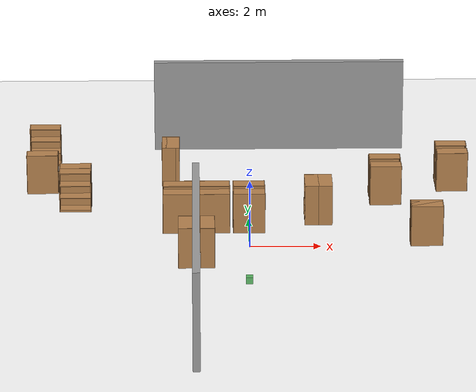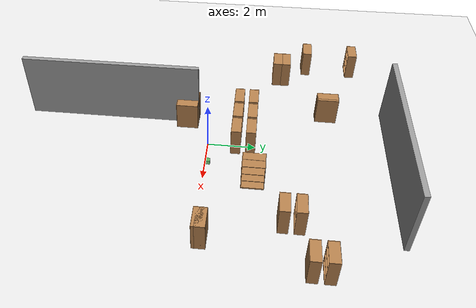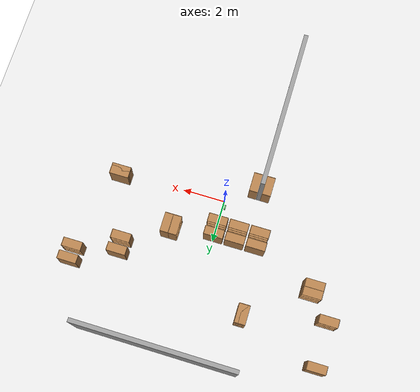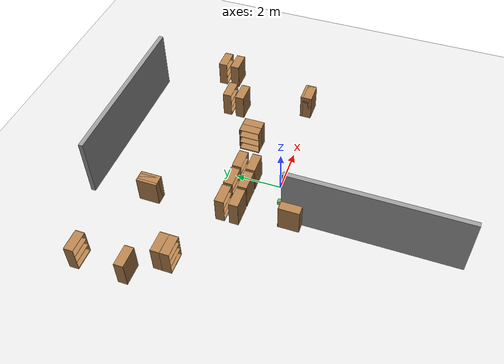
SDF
<sdf version="1.4">
 <world name="default">
  <include><uri>model://sun</uri></include>
  <include><uri>model://ground_plane</uri></include>
  <physics type="ode">
   <max_step_size>0.01</max_step_size>
   <real_time_factor>1</real_time_factor>
   <real_time_update_rate>100</real_time_update_rate>
   <gravity>0 0 -9.8</gravity>
  </physics>
  <model name="rat_goal">
   <static>1</static>
   <link name="rat_goal_link">
    <visual name="visual">
     <geometry><box><size>0.2 0.2 0.2</size></box></geometry>
     <material>
      <script><uri>file://media/materials/scripts/gazebo.material</uri><name>Gazebo/Green</name></script>
     </material>
    </visual>
    <gravity>0</gravity>
   </link>
   <pose>0 0 -1 0 0 0</pose>
  </model>
  <model name="bookshelf">
   <static>1</static>
   <link name="link">
    <inertial><mass>1</mass></inertial>
    <collision name="back">
     <pose>0 0.005 0.6 0 -0 0</pose>
     <geometry><box><size>0.9 0.01 1.2</size></box></geometry>
    </collision>
    <visual name="visual1">
     <pose>0 0.005 0.6 0 -0 0</pose>
     <geometry><box><size>0.9 0.01 1.2</size></box></geometry>
     <material>
      <script><uri>file://media/materials/scripts/gazebo.material</uri><name>Gazebo/Wood</name></script>
     </material>
    </visual>
    <collision name="left_side">
     <pose>0.45 -0.195 0.6 0 -0 0</pose>
     <geometry><box><size>0.02 0.4 1.2</size></box></geometry>
    </collision>
    <visual name="visual2">
     <pose>0.45 -0.195 0.6 0 -0 0</pose>
     <geometry><box><size>0.02 0.4 1.2</size></box></geometry>
     <material>
      <script><uri>file://media/materials/scripts/gazebo.material</uri><name>Gazebo/Wood</name></script>
     </material>
    </visual>
    <collision name="right_side">
     <pose>-0.45 -0.195 0.6 0 -0 0</pose>
     <geometry><box><size>0.02 0.4 1.2</size></box></geometry>
    </collision>
    <visual name="visual3">
     <pose>-0.45 -0.195 0.6 0 -0 0</pose>
     <geometry><box><size>0.02 0.4 1.2</size></box></geometry>
     <material>
      <script><uri>file://media/materials/scripts/gazebo.material</uri><name>Gazebo/Wood</name></script>
     </material>
    </visual>
    <collision name="bottom">
     <pose>0 -0.195 0.03 0 -0 0</pose>
     <geometry><box><size>0.88 0.4 0.06</size></box></geometry>
    </collision>
    <visual name="visual4">
     <pose>0 -0.195 0.03 0 -0 0</pose>
     <geometry><box><size>0.88 0.4 0.06</size></box></geometry>
     <material>
      <script><uri>file://media/materials/scripts/gazebo.material</uri><name>Gazebo/Wood</name></script>
     </material>
    </visual>
    <collision name="top">
     <pose>0 -0.195 1.19 0 -0 0</pose>
     <geometry><box><size>0.88 0.4 0.02</size></box></geometry>
    </collision>
    <visual name="visual5">
     <pose>0 -0.195 1.19 0 -0 0</pose>
     <geometry><box><size>0.88 0.4 0.02</size></box></geometry>
     <material>
      <script><uri>file://media/materials/scripts/gazebo.material</uri><name>Gazebo/Wood</name></script>
     </material>
    </visual>
    <collision name="low_shelf">
     <pose>0 -0.195 0.43 0 -0 0</pose>
     <geometry><box><size>0.88 0.4 0.02</size></box></geometry>
    </collision>
    <visual name="visual6">
     <pose>0 -0.195 0.43 0 -0 0</pose>
     <geometry><box><size>0.88 0.4 0.02</size></box></geometry>
     <material>
      <script><uri>file://media/materials/scripts/gazebo.material</uri><name>Gazebo/Wood</name></script>
     </material>
    </visual>
    <collision name="high_shelf">
     <pose>0 -0.195 0.8 0 -0 0</pose>
     <geometry><box><size>0.88 0.4 0.02</size></box></geometry>
    </collision>
    <visual name="visual7">
     <pose>0 -0.195 0.8 0 -0 0</pose>
     <geometry><box><size>0.88 0.4 0.02</size></box></geometry>
     <material>
      <script><uri>file://media/materials/scripts/gazebo.material</uri><name>Gazebo/Wood</name></script>
     </material>
    </visual>
    <velocity_decay><linear>0</linear><angular>0</angular></velocity_decay>
   </link>
   <pose>-1 2 0 0 -0 0</pose>
  </model>
  <model name="bookshelf_0">
   <static>1</static>
   <link name="link">
    <inertial><mass>1</mass></inertial>
    <collision name="back">
     <pose>0 0.005 0.6 0 -0 0</pose>
     <geometry><box><size>0.9 0.01 1.2</size></box></geometry>
    </collision>
    <visual name="visual1">
     <pose>0 0.005 0.6 0 -0 0</pose>
     <geometry><box><size>0.9 0.01 1.2</size></box></geometry>
     <material>
      <script><uri>file://media/materials/scripts/gazebo.material</uri><name>Gazebo/Wood</name></script>
     </material>
    </visual>
    <collision name="left_side">
     <pose>0.45 -0.195 0.6 0 -0 0</pose>
     <geometry><box><size>0.02 0.4 1.2</size></box></geometry>
    </collision>
    <visual name="visual2">
     <pose>0.45 -0.195 0.6 0 -0 0</pose>
     <geometry><box><size>0.02 0.4 1.2</size></box></geometry>
     <material>
      <script><uri>file://media/materials/scripts/gazebo.material</uri><name>Gazebo/Wood</name></script>
     </material>
    </visual>
    <collision name="right_side">
     <pose>-0.45 -0.195 0.6 0 -0 0</pose>
     <geometry><box><size>0.02 0.4 1.2</size></box></geometry>
    </collision>
    <visual name="visual3">
     <pose>-0.45 -0.195 0.6 0 -0 0</pose>
     <geometry><box><size>0.02 0.4 1.2</size></box></geometry>
     <material>
      <script><uri>file://media/materials/scripts/gazebo.material</uri><name>Gazebo/Wood</name></script>
     </material>
    </visual>
    <collision name="bottom">
     <pose>0 -0.195 0.03 0 -0 0</pose>
     <geometry><box><size>0.88 0.4 0.06</size></box></geometry>
    </collision>
    <visual name="visual4">
     <pose>0 -0.195 0.03 0 -0 0</pose>
     <geometry><box><size>0.88 0.4 0.06</size></box></geometry>
     <material>
      <script><uri>file://media/materials/scripts/gazebo.material</uri><name>Gazebo/Wood</name></script>
     </material>
    </visual>
    <collision name="top">
     <pose>0 -0.195 1.19 0 -0 0</pose>
     <geometry><box><size>0.88 0.4 0.02</size></box></geometry>
    </collision>
    <visual name="visual5">
     <pose>0 -0.195 1.19 0 -0 0</pose>
     <geometry><box><size>0.88 0.4 0.02</size></box></geometry>
     <material>
      <script><uri>file://media/materials/scripts/gazebo.material</uri><name>Gazebo/Wood</name></script>
     </material>
    </visual>
    <collision name="low_shelf">
     <pose>0 -0.195 0.43 0 -0 0</pose>
     <geometry><box><size>0.88 0.4 0.02</size></box></geometry>
    </collision>
    <visual name="visual6">
     <pose>0 -0.195 0.43 0 -0 0</pose>
     <geometry><box><size>0.88 0.4 0.02</size></box></geometry>
     <material>
      <script><uri>file://media/materials/scripts/gazebo.material</uri><name>Gazebo/Wood</name></script>
     </material>
    </visual>
    <collision name="high_shelf">
     <pose>0 -0.195 0.8 0 -0 0</pose>
     <geometry><box><size>0.88 0.4 0.02</size></box></geometry>
    </collision>
    <visual name="visual7">
     <pose>0 -0.195 0.8 0 -0 0</pose>
     <geometry><box><size>0.88 0.4 0.02</size></box></geometry>
     <material>
      <script><uri>file://media/materials/scripts/gazebo.material</uri><name>Gazebo/Wood</name></script>
     </material>
    </visual>
    <velocity_decay><linear>0</linear><angular>0</angular></velocity_decay>
   </link>
   <pose>-2 1 0 0 0 -3.14159</pose>
  </model>
  <model name="bookshelf_1">
   <static>1</static>
   <link name="link">
    <inertial><mass>1</mass></inertial>
    <collision name="back">
     <pose>0 0.005 0.6 0 -0 0</pose>
     <geometry><box><size>0.9 0.01 1.2</size></box></geometry>
    </collision>
    <visual name="visual1">
     <pose>0 0.005 0.6 0 -0 0</pose>
     <geometry><box><size>0.9 0.01 1.2</size></box></geometry>
     <material>
      <script><uri>file://media/materials/scripts/gazebo.material</uri><name>Gazebo/Wood</name></script>
     </material>
    </visual>
    <collision name="left_side">
     <pose>0.45 -0.195 0.6 0 -0 0</pose>
     <geometry><box><size>0.02 0.4 1.2</size></box></geometry>
    </collision>
    <visual name="visual2">
     <pose>0.45 -0.195 0.6 0 -0 0</pose>
     <geometry><box><size>0.02 0.4 1.2</size></box></geometry>
     <material>
      <script><uri>file://media/materials/scripts/gazebo.material</uri><name>Gazebo/Wood</name></script>
     </material>
    </visual>
    <collision name="right_side">
     <pose>-0.45 -0.195 0.6 0 -0 0</pose>
     <geometry><box><size>0.02 0.4 1.2</size></box></geometry>
    </collision>
    <visual name="visual3">
     <pose>-0.45 -0.195 0.6 0 -0 0</pose>
     <geometry><box><size>0.02 0.4 1.2</size></box></geometry>
     <material>
      <script><uri>file://media/materials/scripts/gazebo.material</uri><name>Gazebo/Wood</name></script>
     </material>
    </visual>
    <collision name="bottom">
     <pose>0 -0.195 0.03 0 -0 0</pose>
     <geometry><box><size>0.88 0.4 0.06</size></box></geometry>
    </collision>
    <visual name="visual4">
     <pose>0 -0.195 0.03 0 -0 0</pose>
     <geometry><box><size>0.88 0.4 0.06</size></box></geometry>
     <material>
      <script><uri>file://media/materials/scripts/gazebo.material</uri><name>Gazebo/Wood</name></script>
     </material>
    </visual>
    <collision name="top">
     <pose>0 -0.195 1.19 0 -0 0</pose>
     <geometry><box><size>0.88 0.4 0.02</size></box></geometry>
    </collision>
    <visual name="visual5">
     <pose>0 -0.195 1.19 0 -0 0</pose>
     <geometry><box><size>0.88 0.4 0.02</size></box></geometry>
     <material>
      <script><uri>file://media/materials/scripts/gazebo.material</uri><name>Gazebo/Wood</name></script>
     </material>
    </visual>
    <collision name="low_shelf">
     <pose>0 -0.195 0.43 0 -0 0</pose>
     <geometry><box><size>0.88 0.4 0.02</size></box></geometry>
    </collision>
    <visual name="visual6">
     <pose>0 -0.195 0.43 0 -0 0</pose>
     <geometry><box><size>0.88 0.4 0.02</size></box></geometry>
     <material>
      <script><uri>file://media/materials/scripts/gazebo.material</uri><name>Gazebo/Wood</name></script>
     </material>
    </visual>
    <collision name="high_shelf">
     <pose>0 -0.195 0.8 0 -0 0</pose>
     <geometry><box><size>0.88 0.4 0.02</size></box></geometry>
    </collision>
    <visual name="visual7">
     <pose>0 -0.195 0.8 0 -0 0</pose>
     <geometry><box><size>0.88 0.4 0.02</size></box></geometry>
     <material>
      <script><uri>file://media/materials/scripts/gazebo.material</uri><name>Gazebo/Wood</name></script>
     </material>
    </visual>
    <velocity_decay><linear>0</linear><angular>0</angular></velocity_decay>
   </link>
   <pose>0 2 0 0 -0 0</pose>
  </model>
  <model name="bookshelf_2">
   <static>1</static>
   <link name="link">
    <inertial><mass>1</mass></inertial>
    <collision name="back">
     <pose>0 0.005 0.6 0 -0 0</pose>
     <geometry><box><size>0.9 0.01 1.2</size></box></geometry>
    </collision>
    <visual name="visual1">
     <pose>0 0.005 0.6 0 -0 0</pose>
     <geometry><box><size>0.9 0.01 1.2</size></box></geometry>
     <material>
      <script><uri>file://media/materials/scripts/gazebo.material</uri><name>Gazebo/Wood</name></script>
     </material>
    </visual>
    <collision name="left_side">
     <pose>0.45 -0.195 0.6 0 -0 0</pose>
     <geometry><box><size>0.02 0.4 1.2</size></box></geometry>
    </collision>
    <visual name="visual2">
     <pose>0.45 -0.195 0.6 0 -0 0</pose>
     <geometry><box><size>0.02 0.4 1.2</size></box></geometry>
     <material>
      <script><uri>file://media/materials/scripts/gazebo.material</uri><name>Gazebo/Wood</name></script>
     </material>
    </visual>
    <collision name="right_side">
     <pose>-0.45 -0.195 0.6 0 -0 0</pose>
     <geometry><box><size>0.02 0.4 1.2</size></box></geometry>
    </collision>
    <visual name="visual3">
     <pose>-0.45 -0.195 0.6 0 -0 0</pose>
     <geometry><box><size>0.02 0.4 1.2</size></box></geometry>
     <material>
      <script><uri>file://media/materials/scripts/gazebo.material</uri><name>Gazebo/Wood</name></script>
     </material>
    </visual>
    <collision name="bottom">
     <pose>0 -0.195 0.03 0 -0 0</pose>
     <geometry><box><size>0.88 0.4 0.06</size></box></geometry>
    </collision>
    <visual name="visual4">
     <pose>0 -0.195 0.03 0 -0 0</pose>
     <geometry><box><size>0.88 0.4 0.06</size></box></geometry>
     <material>
      <script><uri>file://media/materials/scripts/gazebo.material</uri><name>Gazebo/Wood</name></script>
     </material>
    </visual>
    <collision name="top">
     <pose>0 -0.195 1.19 0 -0 0</pose>
     <geometry><box><size>0.88 0.4 0.02</size></box></geometry>
    </collision>
    <visual name="visual5">
     <pose>0 -0.195 1.19 0 -0 0</pose>
     <geometry><box><size>0.88 0.4 0.02</size></box></geometry>
     <material>
      <script><uri>file://media/materials/scripts/gazebo.material</uri><name>Gazebo/Wood</name></script>
     </material>
    </visual>
    <collision name="low_shelf">
     <pose>0 -0.195 0.43 0 -0 0</pose>
     <geometry><box><size>0.88 0.4 0.02</size></box></geometry>
    </collision>
    <visual name="visual6">
     <pose>0 -0.195 0.43 0 -0 0</pose>
     <geometry><box><size>0.88 0.4 0.02</size></box></geometry>
     <material>
      <script><uri>file://media/materials/scripts/gazebo.material</uri><name>Gazebo/Wood</name></script>
     </material>
    </visual>
    <collision name="high_shelf">
     <pose>0 -0.195 0.8 0 -0 0</pose>
     <geometry><box><size>0.88 0.4 0.02</size></box></geometry>
    </collision>
    <visual name="visual7">
     <pose>0 -0.195 0.8 0 -0 0</pose>
     <geometry><box><size>0.88 0.4 0.02</size></box></geometry>
     <material>
      <script><uri>file://media/materials/scripts/gazebo.material</uri><name>Gazebo/Wood</name></script>
     </material>
    </visual>
    <velocity_decay><linear>0</linear><angular>0</angular></velocity_decay>
   </link>
   <pose>-2 2 0 0 -0 0</pose>
  </model>
  <model name="bookshelf_3">
   <static>1</static>
   <link name="link">
    <inertial><mass>1</mass></inertial>
    <collision name="back">
     <pose>0 0.005 0.6 0 -0 0</pose>
     <geometry><box><size>0.9 0.01 1.2</size></box></geometry>
    </collision>
    <visual name="visual1">
     <pose>0 0.005 0.6 0 -0 0</pose>
     <geometry><box><size>0.9 0.01 1.2</size></box></geometry>
     <material>
      <script><uri>file://media/materials/scripts/gazebo.material</uri><name>Gazebo/Wood</name></script>
     </material>
    </visual>
    <collision name="left_side">
     <pose>0.45 -0.195 0.6 0 -0 0</pose>
     <geometry><box><size>0.02 0.4 1.2</size></box></geometry>
    </collision>
    <visual name="visual2">
     <pose>0.45 -0.195 0.6 0 -0 0</pose>
     <geometry><box><size>0.02 0.4 1.2</size></box></geometry>
     <material>
      <script><uri>file://media/materials/scripts/gazebo.material</uri><name>Gazebo/Wood</name></script>
     </material>
    </visual>
    <collision name="right_side">
     <pose>-0.45 -0.195 0.6 0 -0 0</pose>
     <geometry><box><size>0.02 0.4 1.2</size></box></geometry>
    </collision>
    <visual name="visual3">
     <pose>-0.45 -0.195 0.6 0 -0 0</pose>
     <geometry><box><size>0.02 0.4 1.2</size></box></geometry>
     <material>
      <script><uri>file://media/materials/scripts/gazebo.material</uri><name>Gazebo/Wood</name></script>
     </material>
    </visual>
    <collision name="bottom">
     <pose>0 -0.195 0.03 0 -0 0</pose>
     <geometry><box><size>0.88 0.4 0.06</size></box></geometry>
    </collision>
    <visual name="visual4">
     <pose>0 -0.195 0.03 0 -0 0</pose>
     <geometry><box><size>0.88 0.4 0.06</size></box></geometry>
     <material>
      <script><uri>file://media/materials/scripts/gazebo.material</uri><name>Gazebo/Wood</name></script>
     </material>
    </visual>
    <collision name="top">
     <pose>0 -0.195 1.19 0 -0 0</pose>
     <geometry><box><size>0.88 0.4 0.02</size></box></geometry>
    </collision>
    <visual name="visual5">
     <pose>0 -0.195 1.19 0 -0 0</pose>
     <geometry><box><size>0.88 0.4 0.02</size></box></geometry>
     <material>
      <script><uri>file://media/materials/scripts/gazebo.material</uri><name>Gazebo/Wood</name></script>
     </material>
    </visual>
    <collision name="low_shelf">
     <pose>0 -0.195 0.43 0 -0 0</pose>
     <geometry><box><size>0.88 0.4 0.02</size></box></geometry>
    </collision>
    <visual name="visual6">
     <pose>0 -0.195 0.43 0 -0 0</pose>
     <geometry><box><size>0.88 0.4 0.02</size></box></geometry>
     <material>
      <script><uri>file://media/materials/scripts/gazebo.material</uri><name>Gazebo/Wood</name></script>
     </material>
    </visual>
    <collision name="high_shelf">
     <pose>0 -0.195 0.8 0 -0 0</pose>
     <geometry><box><size>0.88 0.4 0.02</size></box></geometry>
    </collision>
    <visual name="visual7">
     <pose>0 -0.195 0.8 0 -0 0</pose>
     <geometry><box><size>0.88 0.4 0.02</size></box></geometry>
     <material>
      <script><uri>file://media/materials/scripts/gazebo.material</uri><name>Gazebo/Wood</name></script>
     </material>
    </visual>
    <velocity_decay><linear>0</linear><angular>0</angular></velocity_decay>
   </link>
   <pose>0 1 0 0 0 -3.14159</pose>
  </model>
  <model name="bookshelf_4">
   <static>1</static>
   <link name="link">
    <inertial><mass>1</mass></inertial>
    <collision name="back">
     <pose>0 0.005 0.6 0 -0 0</pose>
     <geometry><box><size>0.9 0.01 1.2</size></box></geometry>
    </collision>
    <visual name="visual1">
     <pose>0 0.005 0.6 0 -0 0</pose>
     <geometry><box><size>0.9 0.01 1.2</size></box></geometry>
     <material>
      <script><uri>file://media/materials/scripts/gazebo.material</uri><name>Gazebo/Wood</name></script>
     </material>
    </visual>
    <collision name="left_side">
     <pose>0.45 -0.195 0.6 0 -0 0</pose>
     <geometry><box><size>0.02 0.4 1.2</size></box></geometry>
    </collision>
    <visual name="visual2">
     <pose>0.45 -0.195 0.6 0 -0 0</pose>
     <geometry><box><size>0.02 0.4 1.2</size></box></geometry>
     <material>
      <script><uri>file://media/materials/scripts/gazebo.material</uri><name>Gazebo/Wood</name></script>
     </material>
    </visual>
    <collision name="right_side">
     <pose>-0.45 -0.195 0.6 0 -0 0</pose>
     <geometry><box><size>0.02 0.4 1.2</size></box></geometry>
    </collision>
    <visual name="visual3">
     <pose>-0.45 -0.195 0.6 0 -0 0</pose>
     <geometry><box><size>0.02 0.4 1.2</size></box></geometry>
     <material>
      <script><uri>file://media/materials/scripts/gazebo.material</uri><name>Gazebo/Wood</name></script>
     </material>
    </visual>
    <collision name="bottom">
     <pose>0 -0.195 0.03 0 -0 0</pose>
     <geometry><box><size>0.88 0.4 0.06</size></box></geometry>
    </collision>
    <visual name="visual4">
     <pose>0 -0.195 0.03 0 -0 0</pose>
     <geometry><box><size>0.88 0.4 0.06</size></box></geometry>
     <material>
      <script><uri>file://media/materials/scripts/gazebo.material</uri><name>Gazebo/Wood</name></script>
     </material>
    </visual>
    <collision name="top">
     <pose>0 -0.195 1.19 0 -0 0</pose>
     <geometry><box><size>0.88 0.4 0.02</size></box></geometry>
    </collision>
    <visual name="visual5">
     <pose>0 -0.195 1.19 0 -0 0</pose>
     <geometry><box><size>0.88 0.4 0.02</size></box></geometry>
     <material>
      <script><uri>file://media/materials/scripts/gazebo.material</uri><name>Gazebo/Wood</name></script>
     </material>
    </visual>
    <collision name="low_shelf">
     <pose>0 -0.195 0.43 0 -0 0</pose>
     <geometry><box><size>0.88 0.4 0.02</size></box></geometry>
    </collision>
    <visual name="visual6">
     <pose>0 -0.195 0.43 0 -0 0</pose>
     <geometry><box><size>0.88 0.4 0.02</size></box></geometry>
     <material>
      <script><uri>file://media/materials/scripts/gazebo.material</uri><name>Gazebo/Wood</name></script>
     </material>
    </visual>
    <collision name="high_shelf">
     <pose>0 -0.195 0.8 0 -0 0</pose>
     <geometry><box><size>0.88 0.4 0.02</size></box></geometry>
    </collision>
    <visual name="visual7">
     <pose>0 -0.195 0.8 0 -0 0</pose>
     <geometry><box><size>0.88 0.4 0.02</size></box></geometry>
     <material>
      <script><uri>file://media/materials/scripts/gazebo.material</uri><name>Gazebo/Wood</name></script>
     </material>
    </visual>
    <velocity_decay><linear>0</linear><angular>0</angular></velocity_decay>
   </link>
   <pose>-1 1 0 0 0 -3.14159</pose>
  </model>
  <model name="grey_wall">
   <static>1</static>
   <link name="link">
    <pose>0 0 1.4 0 -0 0</pose>
    <collision name="collision"><geometry><box><size>7.5 0.2 2.8</size></box></geometry></collision>
    <visual name="visual">
     <cast_shadows>0</cast_shadows>
     <geometry><box><size>7.5 0.2 2.8</size></box></geometry>
     <material>
      <script>
       <uri>model://grey_wall/materials/scripts</uri>
       <uri>model://grey_wall/materials/textures</uri>
       <name>vrc/grey_wall</name>
      </script>
     </material>
    </visual>
    <velocity_decay><linear>0</linear><angular>0</angular></velocity_decay>
   </link>
   <pose>1 7.54791 0 0 -0 0</pose>
  </model>
  <model name="bookshelf_5">
   <static>1</static>
   <link name="link">
    <inertial><mass>1</mass></inertial>
    <collision name="back">
     <pose>0 0.005 0.6 0 -0 0</pose>
     <geometry><box><size>0.9 0.01 1.2</size></box></geometry>
    </collision>
    <visual name="visual1">
     <pose>0 0.005 0.6 0 -0 0</pose>
     <geometry><box><size>0.9 0.01 1.2</size></box></geometry>
     <material>
      <script><uri>file://media/materials/scripts/gazebo.material</uri><name>Gazebo/Wood</name></script>
     </material>
    </visual>
    <collision name="left_side">
     <pose>0.45 -0.195 0.6 0 -0 0</pose>
     <geometry><box><size>0.02 0.4 1.2</size></box></geometry>
    </collision>
    <visual name="visual2">
     <pose>0.45 -0.195 0.6 0 -0 0</pose>
     <geometry><box><size>0.02 0.4 1.2</size></box></geometry>
     <material>
      <script><uri>file://media/materials/scripts/gazebo.material</uri><name>Gazebo/Wood</name></script>
     </material>
    </visual>
    <collision name="right_side">
     <pose>-0.45 -0.195 0.6 0 -0 0</pose>
     <geometry><box><size>0.02 0.4 1.2</size></box></geometry>
    </collision>
    <visual name="visual3">
     <pose>-0.45 -0.195 0.6 0 -0 0</pose>
     <geometry><box><size>0.02 0.4 1.2</size></box></geometry>
     <material>
      <script><uri>file://media/materials/scripts/gazebo.material</uri><name>Gazebo/Wood</name></script>
     </material>
    </visual>
    <collision name="bottom">
     <pose>0 -0.195 0.03 0 -0 0</pose>
     <geometry><box><size>0.88 0.4 0.06</size></box></geometry>
    </collision>
    <visual name="visual4">
     <pose>0 -0.195 0.03 0 -0 0</pose>
     <geometry><box><size>0.88 0.4 0.06</size></box></geometry>
     <material>
      <script><uri>file://media/materials/scripts/gazebo.material</uri><name>Gazebo/Wood</name></script>
     </material>
    </visual>
    <collision name="top">
     <pose>0 -0.195 1.19 0 -0 0</pose>
     <geometry><box><size>0.88 0.4 0.02</size></box></geometry>
    </collision>
    <visual name="visual5">
     <pose>0 -0.195 1.19 0 -0 0</pose>
     <geometry><box><size>0.88 0.4 0.02</size></box></geometry>
     <material>
      <script><uri>file://media/materials/scripts/gazebo.material</uri><name>Gazebo/Wood</name></script>
     </material>
    </visual>
    <collision name="low_shelf">
     <pose>0 -0.195 0.43 0 -0 0</pose>
     <geometry><box><size>0.88 0.4 0.02</size></box></geometry>
    </collision>
    <visual name="visual6">
     <pose>0 -0.195 0.43 0 -0 0</pose>
     <geometry><box><size>0.88 0.4 0.02</size></box></geometry>
     <material>
      <script><uri>file://media/materials/scripts/gazebo.material</uri><name>Gazebo/Wood</name></script>
     </material>
    </visual>
    <collision name="high_shelf">
     <pose>0 -0.195 0.8 0 -0 0</pose>
     <geometry><box><size>0.88 0.4 0.02</size></box></geometry>
    </collision>
    <visual name="visual7">
     <pose>0 -0.195 0.8 0 -0 0</pose>
     <geometry><box><size>0.88 0.4 0.02</size></box></geometry>
     <material>
      <script><uri>file://media/materials/scripts/gazebo.material</uri><name>Gazebo/Wood</name></script>
     </material>
    </visual>
    <velocity_decay><linear>0</linear><angular>0</angular></velocity_decay>
   </link>
   <pose>6 5 0 0 -0 0</pose>
  </model>
  <model name="bookshelf_7">
   <static>1</static>
   <link name="link">
    <inertial><mass>1</mass></inertial>
    <collision name="back">
     <pose>0 0.005 0.6 0 -0 0</pose>
     <geometry><box><size>0.9 0.01 1.2</size></box></geometry>
    </collision>
    <visual name="visual1">
     <pose>0 0.005 0.6 0 -0 0</pose>
     <geometry><box><size>0.9 0.01 1.2</size></box></geometry>
     <material>
      <script><uri>file://media/materials/scripts/gazebo.material</uri><name>Gazebo/Wood</name></script>
     </material>
    </visual>
    <collision name="left_side">
     <pose>0.45 -0.195 0.6 0 -0 0</pose>
     <geometry><box><size>0.02 0.4 1.2</size></box></geometry>
    </collision>
    <visual name="visual2">
     <pose>0.45 -0.195 0.6 0 -0 0</pose>
     <geometry><box><size>0.02 0.4 1.2</size></box></geometry>
     <material>
      <script><uri>file://media/materials/scripts/gazebo.material</uri><name>Gazebo/Wood</name></script>
     </material>
    </visual>
    <collision name="right_side">
     <pose>-0.45 -0.195 0.6 0 -0 0</pose>
     <geometry><box><size>0.02 0.4 1.2</size></box></geometry>
    </collision>
    <visual name="visual3">
     <pose>-0.45 -0.195 0.6 0 -0 0</pose>
     <geometry><box><size>0.02 0.4 1.2</size></box></geometry>
     <material>
      <script><uri>file://media/materials/scripts/gazebo.material</uri><name>Gazebo/Wood</name></script>
     </material>
    </visual>
    <collision name="bottom">
     <pose>0 -0.195 0.03 0 -0 0</pose>
     <geometry><box><size>0.88 0.4 0.06</size></box></geometry>
    </collision>
    <visual name="visual4">
     <pose>0 -0.195 0.03 0 -0 0</pose>
     <geometry><box><size>0.88 0.4 0.06</size></box></geometry>
     <material>
      <script><uri>file://media/materials/scripts/gazebo.material</uri><name>Gazebo/Wood</name></script>
     </material>
    </visual>
    <collision name="top">
     <pose>0 -0.195 1.19 0 -0 0</pose>
     <geometry><box><size>0.88 0.4 0.02</size></box></geometry>
    </collision>
    <visual name="visual5">
     <pose>0 -0.195 1.19 0 -0 0</pose>
     <geometry><box><size>0.88 0.4 0.02</size></box></geometry>
     <material>
      <script><uri>file://media/materials/scripts/gazebo.material</uri><name>Gazebo/Wood</name></script>
     </material>
    </visual>
    <collision name="low_shelf">
     <pose>0 -0.195 0.43 0 -0 0</pose>
     <geometry><box><size>0.88 0.4 0.02</size></box></geometry>
    </collision>
    <visual name="visual6">
     <pose>0 -0.195 0.43 0 -0 0</pose>
     <geometry><box><size>0.88 0.4 0.02</size></box></geometry>
     <material>
      <script><uri>file://media/materials/scripts/gazebo.material</uri><name>Gazebo/Wood</name></script>
     </material>
    </visual>
    <collision name="high_shelf">
     <pose>0 -0.195 0.8 0 -0 0</pose>
     <geometry><box><size>0.88 0.4 0.02</size></box></geometry>
    </collision>
    <visual name="visual7">
     <pose>0 -0.195 0.8 0 -0 0</pose>
     <geometry><box><size>0.88 0.4 0.02</size></box></geometry>
     <material>
      <script><uri>file://media/materials/scripts/gazebo.material</uri><name>Gazebo/Wood</name></script>
     </material>
    </visual>
    <velocity_decay><linear>0</linear><angular>0</angular></velocity_decay>
   </link>
   <pose>6 4 0 0 0 -3.14159</pose>
  </model>
  <model name="bookshelf_8">
   <static>1</static>
   <link name="link">
    <inertial><mass>1</mass></inertial>
    <collision name="back">
     <pose>0 0.005 0.6 0 -0 0</pose>
     <geometry><box><size>0.9 0.01 1.2</size></box></geometry>
    </collision>
    <visual name="visual1">
     <pose>0 0.005 0.6 0 -0 0</pose>
     <geometry><box><size>0.9 0.01 1.2</size></box></geometry>
     <material>
      <script><uri>file://media/materials/scripts/gazebo.material</uri><name>Gazebo/Wood</name></script>
     </material>
    </visual>
    <collision name="left_side">
     <pose>0.45 -0.195 0.6 0 -0 0</pose>
     <geometry><box><size>0.02 0.4 1.2</size></box></geometry>
    </collision>
    <visual name="visual2">
     <pose>0.45 -0.195 0.6 0 -0 0</pose>
     <geometry><box><size>0.02 0.4 1.2</size></box></geometry>
     <material>
      <script><uri>file://media/materials/scripts/gazebo.material</uri><name>Gazebo/Wood</name></script>
     </material>
    </visual>
    <collision name="right_side">
     <pose>-0.45 -0.195 0.6 0 -0 0</pose>
     <geometry><box><size>0.02 0.4 1.2</size></box></geometry>
    </collision>
    <visual name="visual3">
     <pose>-0.45 -0.195 0.6 0 -0 0</pose>
     <geometry><box><size>0.02 0.4 1.2</size></box></geometry>
     <material>
      <script><uri>file://media/materials/scripts/gazebo.material</uri><name>Gazebo/Wood</name></script>
     </material>
    </visual>
    <collision name="bottom">
     <pose>0 -0.195 0.03 0 -0 0</pose>
     <geometry><box><size>0.88 0.4 0.06</size></box></geometry>
    </collision>
    <visual name="visual4">
     <pose>0 -0.195 0.03 0 -0 0</pose>
     <geometry><box><size>0.88 0.4 0.06</size></box></geometry>
     <material>
      <script><uri>file://media/materials/scripts/gazebo.material</uri><name>Gazebo/Wood</name></script>
     </material>
    </visual>
    <collision name="top">
     <pose>0 -0.195 1.19 0 -0 0</pose>
     <geometry><box><size>0.88 0.4 0.02</size></box></geometry>
    </collision>
    <visual name="visual5">
     <pose>0 -0.195 1.19 0 -0 0</pose>
     <geometry><box><size>0.88 0.4 0.02</size></box></geometry>
     <material>
      <script><uri>file://media/materials/scripts/gazebo.material</uri><name>Gazebo/Wood</name></script>
     </material>
    </visual>
    <collision name="low_shelf">
     <pose>0 -0.195 0.43 0 -0 0</pose>
     <geometry><box><size>0.88 0.4 0.02</size></box></geometry>
    </collision>
    <visual name="visual6">
     <pose>0 -0.195 0.43 0 -0 0</pose>
     <geometry><box><size>0.88 0.4 0.02</size></box></geometry>
     <material>
      <script><uri>file://media/materials/scripts/gazebo.material</uri><name>Gazebo/Wood</name></script>
     </material>
    </visual>
    <collision name="high_shelf">
     <pose>0 -0.195 0.8 0 -0 0</pose>
     <geometry><box><size>0.88 0.4 0.02</size></box></geometry>
    </collision>
    <visual name="visual7">
     <pose>0 -0.195 0.8 0 -0 0</pose>
     <geometry><box><size>0.88 0.4 0.02</size></box></geometry>
     <material>
      <script><uri>file://media/materials/scripts/gazebo.material</uri><name>Gazebo/Wood</name></script>
     </material>
    </visual>
    <velocity_decay><linear>0</linear><angular>0</angular></velocity_decay>
   </link>
   <pose>-5 3 0 0 -0 3.14159</pose>
  </model>
  <model name="bookshelf_9">
   <static>1</static>
   <link name="link">
    <inertial><mass>1</mass></inertial>
    <collision name="back">
     <pose>0 0.005 0.6 0 -0 0</pose>
     <geometry><box><size>0.9 0.01 1.2</size></box></geometry>
    </collision>
    <visual name="visual1">
     <pose>0 0.005 0.6 0 -0 0</pose>
     <geometry><box><size>0.9 0.01 1.2</size></box></geometry>
     <material>
      <script><uri>file://media/materials/scripts/gazebo.material</uri><name>Gazebo/Wood</name></script>
     </material>
    </visual>
    <collision name="left_side">
     <pose>0.45 -0.195 0.6 0 -0 0</pose>
     <geometry><box><size>0.02 0.4 1.2</size></box></geometry>
    </collision>
    <visual name="visual2">
     <pose>0.45 -0.195 0.6 0 -0 0</pose>
     <geometry><box><size>0.02 0.4 1.2</size></box></geometry>
     <material>
      <script><uri>file://media/materials/scripts/gazebo.material</uri><name>Gazebo/Wood</name></script>
     </material>
    </visual>
    <collision name="right_side">
     <pose>-0.45 -0.195 0.6 0 -0 0</pose>
     <geometry><box><size>0.02 0.4 1.2</size></box></geometry>
    </collision>
    <visual name="visual3">
     <pose>-0.45 -0.195 0.6 0 -0 0</pose>
     <geometry><box><size>0.02 0.4 1.2</size></box></geometry>
     <material>
      <script><uri>file://media/materials/scripts/gazebo.material</uri><name>Gazebo/Wood</name></script>
     </material>
    </visual>
    <collision name="bottom">
     <pose>0 -0.195 0.03 0 -0 0</pose>
     <geometry><box><size>0.88 0.4 0.06</size></box></geometry>
    </collision>
    <visual name="visual4">
     <pose>0 -0.195 0.03 0 -0 0</pose>
     <geometry><box><size>0.88 0.4 0.06</size></box></geometry>
     <material>
      <script><uri>file://media/materials/scripts/gazebo.material</uri><name>Gazebo/Wood</name></script>
     </material>
    </visual>
    <collision name="top">
     <pose>0 -0.195 1.19 0 -0 0</pose>
     <geometry><box><size>0.88 0.4 0.02</size></box></geometry>
    </collision>
    <visual name="visual5">
     <pose>0 -0.195 1.19 0 -0 0</pose>
     <geometry><box><size>0.88 0.4 0.02</size></box></geometry>
     <material>
      <script><uri>file://media/materials/scripts/gazebo.material</uri><name>Gazebo/Wood</name></script>
     </material>
    </visual>
    <collision name="low_shelf">
     <pose>0 -0.195 0.43 0 -0 0</pose>
     <geometry><box><size>0.88 0.4 0.02</size></box></geometry>
    </collision>
    <visual name="visual6">
     <pose>0 -0.195 0.43 0 -0 0</pose>
     <geometry><box><size>0.88 0.4 0.02</size></box></geometry>
     <material>
      <script><uri>file://media/materials/scripts/gazebo.material</uri><name>Gazebo/Wood</name></script>
     </material>
    </visual>
    <collision name="high_shelf">
     <pose>0 -0.195 0.8 0 -0 0</pose>
     <geometry><box><size>0.88 0.4 0.02</size></box></geometry>
    </collision>
    <visual name="visual7">
     <pose>0 -0.195 0.8 0 -0 0</pose>
     <geometry><box><size>0.88 0.4 0.02</size></box></geometry>
     <material>
      <script><uri>file://media/materials/scripts/gazebo.material</uri><name>Gazebo/Wood</name></script>
     </material>
    </visual>
    <velocity_decay><linear>0</linear><angular>0</angular></velocity_decay>
   </link>
   <pose>-5 3 0 0 -0 0</pose>
  </model>
  <model name="bookshelf_10">
   <static>1</static>
   <link name="link">
    <inertial><mass>1</mass></inertial>
    <collision name="back">
     <pose>0 0.005 0.6 0 -0 0</pose>
     <geometry><box><size>0.9 0.01 1.2</size></box></geometry>
    </collision>
    <visual name="visual1">
     <pose>0 0.005 0.6 0 -0 0</pose>
     <geometry><box><size>0.9 0.01 1.2</size></box></geometry>
     <material>
      <script><uri>file://media/materials/scripts/gazebo.material</uri><name>Gazebo/Wood</name></script>
     </material>
    </visual>
    <collision name="left_side">
     <pose>0.45 -0.195 0.6 0 -0 0</pose>
     <geometry><box><size>0.02 0.4 1.2</size></box></geometry>
    </collision>
    <visual name="visual2">
     <pose>0.45 -0.195 0.6 0 -0 0</pose>
     <geometry><box><size>0.02 0.4 1.2</size></box></geometry>
     <material>
      <script><uri>file://media/materials/scripts/gazebo.material</uri><name>Gazebo/Wood</name></script>
     </material>
    </visual>
    <collision name="right_side">
     <pose>-0.45 -0.195 0.6 0 -0 0</pose>
     <geometry><box><size>0.02 0.4 1.2</size></box></geometry>
    </collision>
    <visual name="visual3">
     <pose>-0.45 -0.195 0.6 0 -0 0</pose>
     <geometry><box><size>0.02 0.4 1.2</size></box></geometry>
     <material>
      <script><uri>file://media/materials/scripts/gazebo.material</uri><name>Gazebo/Wood</name></script>
     </material>
    </visual>
    <collision name="bottom">
     <pose>0 -0.195 0.03 0 -0 0</pose>
     <geometry><box><size>0.88 0.4 0.06</size></box></geometry>
    </collision>
    <visual name="visual4">
     <pose>0 -0.195 0.03 0 -0 0</pose>
     <geometry><box><size>0.88 0.4 0.06</size></box></geometry>
     <material>
      <script><uri>file://media/materials/scripts/gazebo.material</uri><name>Gazebo/Wood</name></script>
     </material>
    </visual>
    <collision name="top">
     <pose>0 -0.195 1.19 0 -0 0</pose>
     <geometry><box><size>0.88 0.4 0.02</size></box></geometry>
    </collision>
    <visual name="visual5">
     <pose>0 -0.195 1.19 0 -0 0</pose>
     <geometry><box><size>0.88 0.4 0.02</size></box></geometry>
     <material>
      <script><uri>file://media/materials/scripts/gazebo.material</uri><name>Gazebo/Wood</name></script>
     </material>
    </visual>
    <collision name="low_shelf">
     <pose>0 -0.195 0.43 0 -0 0</pose>
     <geometry><box><size>0.88 0.4 0.02</size></box></geometry>
    </collision>
    <visual name="visual6">
     <pose>0 -0.195 0.43 0 -0 0</pose>
     <geometry><box><size>0.88 0.4 0.02</size></box></geometry>
     <material>
      <script><uri>file://media/materials/scripts/gazebo.material</uri><name>Gazebo/Wood</name></script>
     </material>
    </visual>
    <collision name="high_shelf">
     <pose>0 -0.195 0.8 0 -0 0</pose>
     <geometry><box><size>0.88 0.4 0.02</size></box></geometry>
    </collision>
    <visual name="visual7">
     <pose>0 -0.195 0.8 0 -0 0</pose>
     <geometry><box><size>0.88 0.4 0.02</size></box></geometry>
     <material>
      <script><uri>file://media/materials/scripts/gazebo.material</uri><name>Gazebo/Wood</name></script>
     </material>
    </visual>
    <velocity_decay><linear>0</linear><angular>0</angular></velocity_decay>
   </link>
   <pose>-2 -1 0 0 -0 1.5708</pose>
  </model>
  <model name="bookshelf_11">
   <static>1</static>
   <link name="link">
    <inertial><mass>1</mass></inertial>
    <collision name="back">
     <pose>0 0.005 0.6 0 -0 0</pose>
     <geometry><box><size>0.9 0.01 1.2</size></box></geometry>
    </collision>
    <visual name="visual1">
     <pose>0 0.005 0.6 0 -0 0</pose>
     <geometry><box><size>0.9 0.01 1.2</size></box></geometry>
     <material>
      <script><uri>file://media/materials/scripts/gazebo.material</uri><name>Gazebo/Wood</name></script>
     </material>
    </visual>
    <collision name="left_side">
     <pose>0.45 -0.195 0.6 0 -0 0</pose>
     <geometry><box><size>0.02 0.4 1.2</size></box></geometry>
    </collision>
    <visual name="visual2">
     <pose>0.45 -0.195 0.6 0 -0 0</pose>
     <geometry><box><size>0.02 0.4 1.2</size></box></geometry>
     <material>
      <script><uri>file://media/materials/scripts/gazebo.material</uri><name>Gazebo/Wood</name></script>
     </material>
    </visual>
    <collision name="right_side">
     <pose>-0.45 -0.195 0.6 0 -0 0</pose>
     <geometry><box><size>0.02 0.4 1.2</size></box></geometry>
    </collision>
    <visual name="visual3">
     <pose>-0.45 -0.195 0.6 0 -0 0</pose>
     <geometry><box><size>0.02 0.4 1.2</size></box></geometry>
     <material>
      <script><uri>file://media/materials/scripts/gazebo.material</uri><name>Gazebo/Wood</name></script>
     </material>
    </visual>
    <collision name="bottom">
     <pose>0 -0.195 0.03 0 -0 0</pose>
     <geometry><box><size>0.88 0.4 0.06</size></box></geometry>
    </collision>
    <visual name="visual4">
     <pose>0 -0.195 0.03 0 -0 0</pose>
     <geometry><box><size>0.88 0.4 0.06</size></box></geometry>
     <material>
      <script><uri>file://media/materials/scripts/gazebo.material</uri><name>Gazebo/Wood</name></script>
     </material>
    </visual>
    <collision name="top">
     <pose>0 -0.195 1.19 0 -0 0</pose>
     <geometry><box><size>0.88 0.4 0.02</size></box></geometry>
    </collision>
    <visual name="visual5">
     <pose>0 -0.195 1.19 0 -0 0</pose>
     <geometry><box><size>0.88 0.4 0.02</size></box></geometry>
     <material>
      <script><uri>file://media/materials/scripts/gazebo.material</uri><name>Gazebo/Wood</name></script>
     </material>
    </visual>
    <collision name="low_shelf">
     <pose>0 -0.195 0.43 0 -0 0</pose>
     <geometry><box><size>0.88 0.4 0.02</size></box></geometry>
    </collision>
    <visual name="visual6">
     <pose>0 -0.195 0.43 0 -0 0</pose>
     <geometry><box><size>0.88 0.4 0.02</size></box></geometry>
     <material>
      <script><uri>file://media/materials/scripts/gazebo.material</uri><name>Gazebo/Wood</name></script>
     </material>
    </visual>
    <collision name="high_shelf">
     <pose>0 -0.195 0.8 0 -0 0</pose>
     <geometry><box><size>0.88 0.4 0.02</size></box></geometry>
    </collision>
    <visual name="visual7">
     <pose>0 -0.195 0.8 0 -0 0</pose>
     <geometry><box><size>0.88 0.4 0.02</size></box></geometry>
     <material>
      <script><uri>file://media/materials/scripts/gazebo.material</uri><name>Gazebo/Wood</name></script>
     </material>
    </visual>
    <velocity_decay><linear>0</linear><angular>0</angular></velocity_decay>
   </link>
   <pose>-1 -1 0 0 0 -1.5708</pose>
  </model>
  <model name="grey_wall_0">
   <static>1</static>
   <link name="link">
    <pose>0 0 1.4 0 -0 0</pose>
    <collision name="collision"><geometry><box><size>7.5 0.2 2.8</size></box></geometry></collision>
    <visual name="visual">
     <cast_shadows>0</cast_shadows>
     <geometry><box><size>7.5 0.2 2.8</size></box></geometry>
     <material>
      <script>
       <uri>model://grey_wall/materials/scripts</uri>
       <uri>model://grey_wall/materials/textures</uri>
       <name>vrc/grey_wall</name>
      </script>
     </material>
    </visual>
    <velocity_decay><linear>0</linear><angular>0</angular></velocity_decay>
   </link>
   <pose>-1.50961 -4.29402 0 0 -0 1.5708</pose>
  </model>
  <model name="bookshelf_12">
   <static>1</static>
   <link name="link">
    <inertial><mass>1</mass></inertial>
    <collision name="back">
     <pose>0 0.005 0.6 0 -0 0</pose>
     <geometry><box><size>0.9 0.01 1.2</size></box></geometry>
    </collision>
    <visual name="visual1">
     <pose>0 0.005 0.6 0 -0 0</pose>
     <geometry><box><size>0.9 0.01 1.2</size></box></geometry>
     <material>
      <script><uri>file://media/materials/scripts/gazebo.material</uri><name>Gazebo/Wood</name></script>
     </material>
    </visual>
    <collision name="left_side">
     <pose>0.45 -0.195 0.6 0 -0 0</pose>
     <geometry><box><size>0.02 0.4 1.2</size></box></geometry>
    </collision>
    <visual name="visual2">
     <pose>0.45 -0.195 0.6 0 -0 0</pose>
     <geometry><box><size>0.02 0.4 1.2</size></box></geometry>
     <material>
      <script><uri>file://media/materials/scripts/gazebo.material</uri><name>Gazebo/Wood</name></script>
     </material>
    </visual>
    <collision name="right_side">
     <pose>-0.45 -0.195 0.6 0 -0 0</pose>
     <geometry><box><size>0.02 0.4 1.2</size></box></geometry>
    </collision>
    <visual name="visual3">
     <pose>-0.45 -0.195 0.6 0 -0 0</pose>
     <geometry><box><size>0.02 0.4 1.2</size></box></geometry>
     <material>
      <script><uri>file://media/materials/scripts/gazebo.material</uri><name>Gazebo/Wood</name></script>
     </material>
    </visual>
    <collision name="bottom">
     <pose>0 -0.195 0.03 0 -0 0</pose>
     <geometry><box><size>0.88 0.4 0.06</size></box></geometry>
    </collision>
    <visual name="visual4">
     <pose>0 -0.195 0.03 0 -0 0</pose>
     <geometry><box><size>0.88 0.4 0.06</size></box></geometry>
     <material>
      <script><uri>file://media/materials/scripts/gazebo.material</uri><name>Gazebo/Wood</name></script>
     </material>
    </visual>
    <collision name="top">
     <pose>0 -0.195 1.19 0 -0 0</pose>
     <geometry><box><size>0.88 0.4 0.02</size></box></geometry>
    </collision>
    <visual name="visual5">
     <pose>0 -0.195 1.19 0 -0 0</pose>
     <geometry><box><size>0.88 0.4 0.02</size></box></geometry>
     <material>
      <script><uri>file://media/materials/scripts/gazebo.material</uri><name>Gazebo/Wood</name></script>
     </material>
    </visual>
    <collision name="low_shelf">
     <pose>0 -0.195 0.43 0 -0 0</pose>
     <geometry><box><size>0.88 0.4 0.02</size></box></geometry>
    </collision>
    <visual name="visual6">
     <pose>0 -0.195 0.43 0 -0 0</pose>
     <geometry><box><size>0.88 0.4 0.02</size></box></geometry>
     <material>
      <script><uri>file://media/materials/scripts/gazebo.material</uri><name>Gazebo/Wood</name></script>
     </material>
    </visual>
    <collision name="high_shelf">
     <pose>0 -0.195 0.8 0 -0 0</pose>
     <geometry><box><size>0.88 0.4 0.02</size></box></geometry>
    </collision>
    <visual name="visual7">
     <pose>0 -0.195 0.8 0 -0 0</pose>
     <geometry><box><size>0.88 0.4 0.02</size></box></geometry>
     <material>
      <script><uri>file://media/materials/scripts/gazebo.material</uri><name>Gazebo/Wood</name></script>
     </material>
    </visual>
    <velocity_decay><linear>0</linear><angular>0</angular></velocity_decay>
   </link>
   <pose>4 4 0 0 -0 0</pose>
  </model>
  <model name="bookshelf_13">
   <static>1</static>
   <link name="link">
    <inertial><mass>1</mass></inertial>
    <collision name="back">
     <pose>0 0.005 0.6 0 -0 0</pose>
     <geometry><box><size>0.9 0.01 1.2</size></box></geometry>
    </collision>
    <visual name="visual1">
     <pose>0 0.005 0.6 0 -0 0</pose>
     <geometry><box><size>0.9 0.01 1.2</size></box></geometry>
     <material>
      <script><uri>file://media/materials/scripts/gazebo.material</uri><name>Gazebo/Wood</name></script>
     </material>
    </visual>
    <collision name="left_side">
     <pose>0.45 -0.195 0.6 0 -0 0</pose>
     <geometry><box><size>0.02 0.4 1.2</size></box></geometry>
    </collision>
    <visual name="visual2">
     <pose>0.45 -0.195 0.6 0 -0 0</pose>
     <geometry><box><size>0.02 0.4 1.2</size></box></geometry>
     <material>
      <script><uri>file://media/materials/scripts/gazebo.material</uri><name>Gazebo/Wood</name></script>
     </material>
    </visual>
    <collision name="right_side">
     <pose>-0.45 -0.195 0.6 0 -0 0</pose>
     <geometry><box><size>0.02 0.4 1.2</size></box></geometry>
    </collision>
    <visual name="visual3">
     <pose>-0.45 -0.195 0.6 0 -0 0</pose>
     <geometry><box><size>0.02 0.4 1.2</size></box></geometry>
     <material>
      <script><uri>file://media/materials/scripts/gazebo.material</uri><name>Gazebo/Wood</name></script>
     </material>
    </visual>
    <collision name="bottom">
     <pose>0 -0.195 0.03 0 -0 0</pose>
     <geometry><box><size>0.88 0.4 0.06</size></box></geometry>
    </collision>
    <visual name="visual4">
     <pose>0 -0.195 0.03 0 -0 0</pose>
     <geometry><box><size>0.88 0.4 0.06</size></box></geometry>
     <material>
      <script><uri>file://media/materials/scripts/gazebo.material</uri><name>Gazebo/Wood</name></script>
     </material>
    </visual>
    <collision name="top">
     <pose>0 -0.195 1.19 0 -0 0</pose>
     <geometry><box><size>0.88 0.4 0.02</size></box></geometry>
    </collision>
    <visual name="visual5">
     <pose>0 -0.195 1.19 0 -0 0</pose>
     <geometry><box><size>0.88 0.4 0.02</size></box></geometry>
     <material>
      <script><uri>file://media/materials/scripts/gazebo.material</uri><name>Gazebo/Wood</name></script>
     </material>
    </visual>
    <collision name="low_shelf">
     <pose>0 -0.195 0.43 0 -0 0</pose>
     <geometry><box><size>0.88 0.4 0.02</size></box></geometry>
    </collision>
    <visual name="visual6">
     <pose>0 -0.195 0.43 0 -0 0</pose>
     <geometry><box><size>0.88 0.4 0.02</size></box></geometry>
     <material>
      <script><uri>file://media/materials/scripts/gazebo.material</uri><name>Gazebo/Wood</name></script>
     </material>
    </visual>
    <collision name="high_shelf">
     <pose>0 -0.195 0.8 0 -0 0</pose>
     <geometry><box><size>0.88 0.4 0.02</size></box></geometry>
    </collision>
    <visual name="visual7">
     <pose>0 -0.195 0.8 0 -0 0</pose>
     <geometry><box><size>0.88 0.4 0.02</size></box></geometry>
     <material>
      <script><uri>file://media/materials/scripts/gazebo.material</uri><name>Gazebo/Wood</name></script>
     </material>
    </visual>
    <velocity_decay><linear>0</linear><angular>0</angular></velocity_decay>
   </link>
   <pose>4 3 0 0 -0 3.14159</pose>
  </model>
  <model name="bookshelf_14">
   <static>1</static>
   <link name="link">
    <inertial><mass>1</mass></inertial>
    <collision name="back">
     <pose>0 0.005 0.6 0 -0 0</pose>
     <geometry><box><size>0.9 0.01 1.2</size></box></geometry>
    </collision>
    <visual name="visual1">
     <pose>0 0.005 0.6 0 -0 0</pose>
     <geometry><box><size>0.9 0.01 1.2</size></box></geometry>
     <material>
      <script><uri>file://media/materials/scripts/gazebo.material</uri><name>Gazebo/Wood</name></script>
     </material>
    </visual>
    <collision name="left_side">
     <pose>0.45 -0.195 0.6 0 -0 0</pose>
     <geometry><box><size>0.02 0.4 1.2</size></box></geometry>
    </collision>
    <visual name="visual2">
     <pose>0.45 -0.195 0.6 0 -0 0</pose>
     <geometry><box><size>0.02 0.4 1.2</size></box></geometry>
     <material>
      <script><uri>file://media/materials/scripts/gazebo.material</uri><name>Gazebo/Wood</name></script>
     </material>
    </visual>
    <collision name="right_side">
     <pose>-0.45 -0.195 0.6 0 -0 0</pose>
     <geometry><box><size>0.02 0.4 1.2</size></box></geometry>
    </collision>
    <visual name="visual3">
     <pose>-0.45 -0.195 0.6 0 -0 0</pose>
     <geometry><box><size>0.02 0.4 1.2</size></box></geometry>
     <material>
      <script><uri>file://media/materials/scripts/gazebo.material</uri><name>Gazebo/Wood</name></script>
     </material>
    </visual>
    <collision name="bottom">
     <pose>0 -0.195 0.03 0 -0 0</pose>
     <geometry><box><size>0.88 0.4 0.06</size></box></geometry>
    </collision>
    <visual name="visual4">
     <pose>0 -0.195 0.03 0 -0 0</pose>
     <geometry><box><size>0.88 0.4 0.06</size></box></geometry>
     <material>
      <script><uri>file://media/materials/scripts/gazebo.material</uri><name>Gazebo/Wood</name></script>
     </material>
    </visual>
    <collision name="top">
     <pose>0 -0.195 1.19 0 -0 0</pose>
     <geometry><box><size>0.88 0.4 0.02</size></box></geometry>
    </collision>
    <visual name="visual5">
     <pose>0 -0.195 1.19 0 -0 0</pose>
     <geometry><box><size>0.88 0.4 0.02</size></box></geometry>
     <material>
      <script><uri>file://media/materials/scripts/gazebo.material</uri><name>Gazebo/Wood</name></script>
     </material>
    </visual>
    <collision name="low_shelf">
     <pose>0 -0.195 0.43 0 -0 0</pose>
     <geometry><box><size>0.88 0.4 0.02</size></box></geometry>
    </collision>
    <visual name="visual6">
     <pose>0 -0.195 0.43 0 -0 0</pose>
     <geometry><box><size>0.88 0.4 0.02</size></box></geometry>
     <material>
      <script><uri>file://media/materials/scripts/gazebo.material</uri><name>Gazebo/Wood</name></script>
     </material>
    </visual>
    <collision name="high_shelf">
     <pose>0 -0.195 0.8 0 -0 0</pose>
     <geometry><box><size>0.88 0.4 0.02</size></box></geometry>
    </collision>
    <visual name="visual7">
     <pose>0 -0.195 0.8 0 -0 0</pose>
     <geometry><box><size>0.88 0.4 0.02</size></box></geometry>
     <material>
      <script><uri>file://media/materials/scripts/gazebo.material</uri><name>Gazebo/Wood</name></script>
     </material>
    </visual>
    <velocity_decay><linear>0</linear><angular>0</angular></velocity_decay>
   </link>
   <pose>2 2 0 0 0 -1.5708</pose>
  </model>
  <model name="bookshelf_15">
   <static>1</static>
   <link name="link">
    <inertial><mass>1</mass></inertial>
    <collision name="back">
     <pose>0 0.005 0.6 0 -0 0</pose>
     <geometry><box><size>0.9 0.01 1.2</size></box></geometry>
    </collision>
    <visual name="visual1">
     <pose>0 0.005 0.6 0 -0 0</pose>
     <geometry><box><size>0.9 0.01 1.2</size></box></geometry>
     <material>
      <script><uri>file://media/materials/scripts/gazebo.material</uri><name>Gazebo/Wood</name></script>
     </material>
    </visual>
    <collision name="left_side">
     <pose>0.45 -0.195 0.6 0 -0 0</pose>
     <geometry><box><size>0.02 0.4 1.2</size></box></geometry>
    </collision>
    <visual name="visual2">
     <pose>0.45 -0.195 0.6 0 -0 0</pose>
     <geometry><box><size>0.02 0.4 1.2</size></box></geometry>
     <material>
      <script><uri>file://media/materials/scripts/gazebo.material</uri><name>Gazebo/Wood</name></script>
     </material>
    </visual>
    <collision name="right_side">
     <pose>-0.45 -0.195 0.6 0 -0 0</pose>
     <geometry><box><size>0.02 0.4 1.2</size></box></geometry>
    </collision>
    <visual name="visual3">
     <pose>-0.45 -0.195 0.6 0 -0 0</pose>
     <geometry><box><size>0.02 0.4 1.2</size></box></geometry>
     <material>
      <script><uri>file://media/materials/scripts/gazebo.material</uri><name>Gazebo/Wood</name></script>
     </material>
    </visual>
    <collision name="bottom">
     <pose>0 -0.195 0.03 0 -0 0</pose>
     <geometry><box><size>0.88 0.4 0.06</size></box></geometry>
    </collision>
    <visual name="visual4">
     <pose>0 -0.195 0.03 0 -0 0</pose>
     <geometry><box><size>0.88 0.4 0.06</size></box></geometry>
     <material>
      <script><uri>file://media/materials/scripts/gazebo.material</uri><name>Gazebo/Wood</name></script>
     </material>
    </visual>
    <collision name="top">
     <pose>0 -0.195 1.19 0 -0 0</pose>
     <geometry><box><size>0.88 0.4 0.02</size></box></geometry>
    </collision>
    <visual name="visual5">
     <pose>0 -0.195 1.19 0 -0 0</pose>
     <geometry><box><size>0.88 0.4 0.02</size></box></geometry>
     <material>
      <script><uri>file://media/materials/scripts/gazebo.material</uri><name>Gazebo/Wood</name></script>
     </material>
    </visual>
    <collision name="low_shelf">
     <pose>0 -0.195 0.43 0 -0 0</pose>
     <geometry><box><size>0.88 0.4 0.02</size></box></geometry>
    </collision>
    <visual name="visual6">
     <pose>0 -0.195 0.43 0 -0 0</pose>
     <geometry><box><size>0.88 0.4 0.02</size></box></geometry>
     <material>
      <script><uri>file://media/materials/scripts/gazebo.material</uri><name>Gazebo/Wood</name></script>
     </material>
    </visual>
    <collision name="high_shelf">
     <pose>0 -0.195 0.8 0 -0 0</pose>
     <geometry><box><size>0.88 0.4 0.02</size></box></geometry>
    </collision>
    <visual name="visual7">
     <pose>0 -0.195 0.8 0 -0 0</pose>
     <geometry><box><size>0.88 0.4 0.02</size></box></geometry>
     <material>
      <script><uri>file://media/materials/scripts/gazebo.material</uri><name>Gazebo/Wood</name></script>
     </material>
    </visual>
    <velocity_decay><linear>0</linear><angular>0</angular></velocity_decay>
   </link>
   <pose>2 2 0 0 -0 1.5708</pose>
  </model>
  <model name="bookshelf_16">
   <static>1</static>
   <link name="link">
    <inertial><mass>1</mass></inertial>
    <collision name="back">
     <pose>0 0.005 0.6 0 -0 0</pose>
     <geometry><box><size>0.9 0.01 1.2</size></box></geometry>
    </collision>
    <visual name="visual1">
     <pose>0 0.005 0.6 0 -0 0</pose>
     <geometry><box><size>0.9 0.01 1.2</size></box></geometry>
     <material>
      <script><uri>file://media/materials/scripts/gazebo.material</uri><name>Gazebo/Wood</name></script>
     </material>
    </visual>
    <collision name="left_side">
     <pose>0.45 -0.195 0.6 0 -0 0</pose>
     <geometry><box><size>0.02 0.4 1.2</size></box></geometry>
    </collision>
    <visual name="visual2">
     <pose>0.45 -0.195 0.6 0 -0 0</pose>
     <geometry><box><size>0.02 0.4 1.2</size></box></geometry>
     <material>
      <script><uri>file://media/materials/scripts/gazebo.material</uri><name>Gazebo/Wood</name></script>
     </material>
    </visual>
    <collision name="right_side">
     <pose>-0.45 -0.195 0.6 0 -0 0</pose>
     <geometry><box><size>0.02 0.4 1.2</size></box></geometry>
    </collision>
    <visual name="visual3">
     <pose>-0.45 -0.195 0.6 0 -0 0</pose>
     <geometry><box><size>0.02 0.4 1.2</size></box></geometry>
     <material>
      <script><uri>file://media/materials/scripts/gazebo.material</uri><name>Gazebo/Wood</name></script>
     </material>
    </visual>
    <collision name="bottom">
     <pose>0 -0.195 0.03 0 -0 0</pose>
     <geometry><box><size>0.88 0.4 0.06</size></box></geometry>
    </collision>
    <visual name="visual4">
     <pose>0 -0.195 0.03 0 -0 0</pose>
     <geometry><box><size>0.88 0.4 0.06</size></box></geometry>
     <material>
      <script><uri>file://media/materials/scripts/gazebo.material</uri><name>Gazebo/Wood</name></script>
     </material>
    </visual>
    <collision name="top">
     <pose>0 -0.195 1.19 0 -0 0</pose>
     <geometry><box><size>0.88 0.4 0.02</size></box></geometry>
    </collision>
    <visual name="visual5">
     <pose>0 -0.195 1.19 0 -0 0</pose>
     <geometry><box><size>0.88 0.4 0.02</size></box></geometry>
     <material>
      <script><uri>file://media/materials/scripts/gazebo.material</uri><name>Gazebo/Wood</name></script>
     </material>
    </visual>
    <collision name="low_shelf">
     <pose>0 -0.195 0.43 0 -0 0</pose>
     <geometry><box><size>0.88 0.4 0.02</size></box></geometry>
    </collision>
    <visual name="visual6">
     <pose>0 -0.195 0.43 0 -0 0</pose>
     <geometry><box><size>0.88 0.4 0.02</size></box></geometry>
     <material>
      <script><uri>file://media/materials/scripts/gazebo.material</uri><name>Gazebo/Wood</name></script>
     </material>
    </visual>
    <collision name="high_shelf">
     <pose>0 -0.195 0.8 0 -0 0</pose>
     <geometry><box><size>0.88 0.4 0.02</size></box></geometry>
    </collision>
    <visual name="visual7">
     <pose>0 -0.195 0.8 0 -0 0</pose>
     <geometry><box><size>0.88 0.4 0.02</size></box></geometry>
     <material>
      <script><uri>file://media/materials/scripts/gazebo.material</uri><name>Gazebo/Wood</name></script>
     </material>
    </visual>
    <velocity_decay><linear>0</linear><angular>0</angular></velocity_decay>
   </link>
   <pose>5 0.5 0 0 -0 0</pose>
  </model>
  <model name="bookshelf_17">
   <static>1</static>
   <link name="link">
    <inertial><mass>1</mass></inertial>
    <collision name="back">
     <pose>0 0.005 0.6 0 -0 0</pose>
     <geometry><box><size>0.9 0.01 1.2</size></box></geometry>
    </collision>
    <visual name="visual1">
     <pose>0 0.005 0.6 0 -0 0</pose>
     <geometry><box><size>0.9 0.01 1.2</size></box></geometry>
     <material>
      <script><uri>file://media/materials/scripts/gazebo.material</uri><name>Gazebo/Wood</name></script>
     </material>
    </visual>
    <collision name="left_side">
     <pose>0.45 -0.195 0.6 0 -0 0</pose>
     <geometry><box><size>0.02 0.4 1.2</size></box></geometry>
    </collision>
    <visual name="visual2">
     <pose>0.45 -0.195 0.6 0 -0 0</pose>
     <geometry><box><size>0.02 0.4 1.2</size></box></geometry>
     <material>
      <script><uri>file://media/materials/scripts/gazebo.material</uri><name>Gazebo/Wood</name></script>
     </material>
    </visual>
    <collision name="right_side">
     <pose>-0.45 -0.195 0.6 0 -0 0</pose>
     <geometry><box><size>0.02 0.4 1.2</size></box></geometry>
    </collision>
    <visual name="visual3">
     <pose>-0.45 -0.195 0.6 0 -0 0</pose>
     <geometry><box><size>0.02 0.4 1.2</size></box></geometry>
     <material>
      <script><uri>file://media/materials/scripts/gazebo.material</uri><name>Gazebo/Wood</name></script>
     </material>
    </visual>
    <collision name="bottom">
     <pose>0 -0.195 0.03 0 -0 0</pose>
     <geometry><box><size>0.88 0.4 0.06</size></box></geometry>
    </collision>
    <visual name="visual4">
     <pose>0 -0.195 0.03 0 -0 0</pose>
     <geometry><box><size>0.88 0.4 0.06</size></box></geometry>
     <material>
      <script><uri>file://media/materials/scripts/gazebo.material</uri><name>Gazebo/Wood</name></script>
     </material>
    </visual>
    <collision name="top">
     <pose>0 -0.195 1.19 0 -0 0</pose>
     <geometry><box><size>0.88 0.4 0.02</size></box></geometry>
    </collision>
    <visual name="visual5">
     <pose>0 -0.195 1.19 0 -0 0</pose>
     <geometry><box><size>0.88 0.4 0.02</size></box></geometry>
     <material>
      <script><uri>file://media/materials/scripts/gazebo.material</uri><name>Gazebo/Wood</name></script>
     </material>
    </visual>
    <collision name="low_shelf">
     <pose>0 -0.195 0.43 0 -0 0</pose>
     <geometry><box><size>0.88 0.4 0.02</size></box></geometry>
    </collision>
    <visual name="visual6">
     <pose>0 -0.195 0.43 0 -0 0</pose>
     <geometry><box><size>0.88 0.4 0.02</size></box></geometry>
     <material>
      <script><uri>file://media/materials/scripts/gazebo.material</uri><name>Gazebo/Wood</name></script>
     </material>
    </visual>
    <collision name="high_shelf">
     <pose>0 -0.195 0.8 0 -0 0</pose>
     <geometry><box><size>0.88 0.4 0.02</size></box></geometry>
    </collision>
    <visual name="visual7">
     <pose>0 -0.195 0.8 0 -0 0</pose>
     <geometry><box><size>0.88 0.4 0.02</size></box></geometry>
     <material>
      <script><uri>file://media/materials/scripts/gazebo.material</uri><name>Gazebo/Wood</name></script>
     </material>
    </visual>
    <velocity_decay><linear>0</linear><angular>0</angular></velocity_decay>
   </link>
   <pose>5 0 0 0 0 -3.14159</pose>
  </model>
  <model name="bookshelf_18">
   <static>1</static>
   <link name="link">
    <inertial><mass>1</mass></inertial>
    <collision name="back">
     <pose>0 0.005 0.6 0 -0 0</pose>
     <geometry><box><size>0.9 0.01 1.2</size></box></geometry>
    </collision>
    <visual name="visual1">
     <pose>0 0.005 0.6 0 -0 0</pose>
     <geometry><box><size>0.9 0.01 1.2</size></box></geometry>
     <material>
      <script><uri>file://media/materials/scripts/gazebo.material</uri><name>Gazebo/Wood</name></script>
     </material>
    </visual>
    <collision name="left_side">
     <pose>0.45 -0.195 0.6 0 -0 0</pose>
     <geometry><box><size>0.02 0.4 1.2</size></box></geometry>
    </collision>
    <visual name="visual2">
     <pose>0.45 -0.195 0.6 0 -0 0</pose>
     <geometry><box><size>0.02 0.4 1.2</size></box></geometry>
     <material>
      <script><uri>file://media/materials/scripts/gazebo.material</uri><name>Gazebo/Wood</name></script>
     </material>
    </visual>
    <collision name="right_side">
     <pose>-0.45 -0.195 0.6 0 -0 0</pose>
     <geometry><box><size>0.02 0.4 1.2</size></box></geometry>
    </collision>
    <visual name="visual3">
     <pose>-0.45 -0.195 0.6 0 -0 0</pose>
     <geometry><box><size>0.02 0.4 1.2</size></box></geometry>
     <material>
      <script><uri>file://media/materials/scripts/gazebo.material</uri><name>Gazebo/Wood</name></script>
     </material>
    </visual>
    <collision name="bottom">
     <pose>0 -0.195 0.03 0 -0 0</pose>
     <geometry><box><size>0.88 0.4 0.06</size></box></geometry>
    </collision>
    <visual name="visual4">
     <pose>0 -0.195 0.03 0 -0 0</pose>
     <geometry><box><size>0.88 0.4 0.06</size></box></geometry>
     <material>
      <script><uri>file://media/materials/scripts/gazebo.material</uri><name>Gazebo/Wood</name></script>
     </material>
    </visual>
    <collision name="top">
     <pose>0 -0.195 1.19 0 -0 0</pose>
     <geometry><box><size>0.88 0.4 0.02</size></box></geometry>
    </collision>
    <visual name="visual5">
     <pose>0 -0.195 1.19 0 -0 0</pose>
     <geometry><box><size>0.88 0.4 0.02</size></box></geometry>
     <material>
      <script><uri>file://media/materials/scripts/gazebo.material</uri><name>Gazebo/Wood</name></script>
     </material>
    </visual>
    <collision name="low_shelf">
     <pose>0 -0.195 0.43 0 -0 0</pose>
     <geometry><box><size>0.88 0.4 0.02</size></box></geometry>
    </collision>
    <visual name="visual6">
     <pose>0 -0.195 0.43 0 -0 0</pose>
     <geometry><box><size>0.88 0.4 0.02</size></box></geometry>
     <material>
      <script><uri>file://media/materials/scripts/gazebo.material</uri><name>Gazebo/Wood</name></script>
     </material>
    </visual>
    <collision name="high_shelf">
     <pose>0 -0.195 0.8 0 -0 0</pose>
     <geometry><box><size>0.88 0.4 0.02</size></box></geometry>
    </collision>
    <visual name="visual7">
     <pose>0 -0.195 0.8 0 -0 0</pose>
     <geometry><box><size>0.88 0.4 0.02</size></box></geometry>
     <material>
      <script><uri>file://media/materials/scripts/gazebo.material</uri><name>Gazebo/Wood</name></script>
     </material>
    </visual>
    <velocity_decay><linear>0</linear><angular>0</angular></velocity_decay>
   </link>
   <pose>-2 5 0 0 0 -1.5708</pose>
  </model>
  <model name="bookshelf_19">
   <static>1</static>
   <link name="link">
    <inertial><mass>1</mass></inertial>
    <collision name="back">
     <pose>0 0.005 0.6 0 -0 0</pose>
     <geometry><box><size>0.9 0.01 1.2</size></box></geometry>
    </collision>
    <visual name="visual1">
     <pose>0 0.005 0.6 0 -0 0</pose>
     <geometry><box><size>0.9 0.01 1.2</size></box></geometry>
     <material>
      <script><uri>file://media/materials/scripts/gazebo.material</uri><name>Gazebo/Wood</name></script>
     </material>
    </visual>
    <collision name="left_side">
     <pose>0.45 -0.195 0.6 0 -0 0</pose>
     <geometry><box><size>0.02 0.4 1.2</size></box></geometry>
    </collision>
    <visual name="visual2">
     <pose>0.45 -0.195 0.6 0 -0 0</pose>
     <geometry><box><size>0.02 0.4 1.2</size></box></geometry>
     <material>
      <script><uri>file://media/materials/scripts/gazebo.material</uri><name>Gazebo/Wood</name></script>
     </material>
    </visual>
    <collision name="right_side">
     <pose>-0.45 -0.195 0.6 0 -0 0</pose>
     <geometry><box><size>0.02 0.4 1.2</size></box></geometry>
    </collision>
    <visual name="visual3">
     <pose>-0.45 -0.195 0.6 0 -0 0</pose>
     <geometry><box><size>0.02 0.4 1.2</size></box></geometry>
     <material>
      <script><uri>file://media/materials/scripts/gazebo.material</uri><name>Gazebo/Wood</name></script>
     </material>
    </visual>
    <collision name="bottom">
     <pose>0 -0.195 0.03 0 -0 0</pose>
     <geometry><box><size>0.88 0.4 0.06</size></box></geometry>
    </collision>
    <visual name="visual4">
     <pose>0 -0.195 0.03 0 -0 0</pose>
     <geometry><box><size>0.88 0.4 0.06</size></box></geometry>
     <material>
      <script><uri>file://media/materials/scripts/gazebo.material</uri><name>Gazebo/Wood</name></script>
     </material>
    </visual>
    <collision name="top">
     <pose>0 -0.195 1.19 0 -0 0</pose>
     <geometry><box><size>0.88 0.4 0.02</size></box></geometry>
    </collision>
    <visual name="visual5">
     <pose>0 -0.195 1.19 0 -0 0</pose>
     <geometry><box><size>0.88 0.4 0.02</size></box></geometry>
     <material>
      <script><uri>file://media/materials/scripts/gazebo.material</uri><name>Gazebo/Wood</name></script>
     </material>
    </visual>
    <collision name="low_shelf">
     <pose>0 -0.195 0.43 0 -0 0</pose>
     <geometry><box><size>0.88 0.4 0.02</size></box></geometry>
    </collision>
    <visual name="visual6">
     <pose>0 -0.195 0.43 0 -0 0</pose>
     <geometry><box><size>0.88 0.4 0.02</size></box></geometry>
     <material>
      <script><uri>file://media/materials/scripts/gazebo.material</uri><name>Gazebo/Wood</name></script>
     </material>
    </visual>
    <collision name="high_shelf">
     <pose>0 -0.195 0.8 0 -0 0</pose>
     <geometry><box><size>0.88 0.4 0.02</size></box></geometry>
    </collision>
    <visual name="visual7">
     <pose>0 -0.195 0.8 0 -0 0</pose>
     <geometry><box><size>0.88 0.4 0.02</size></box></geometry>
     <material>
      <script><uri>file://media/materials/scripts/gazebo.material</uri><name>Gazebo/Wood</name></script>
     </material>
    </visual>
    <velocity_decay><linear>0</linear><angular>0</angular></velocity_decay>
   </link>
   <pose>-2.5 5 0 0 -0 1.5708</pose>
  </model>
  <model name="bookshelf_20">
   <static>1</static>
   <link name="link">
    <inertial><mass>1</mass></inertial>
    <collision name="back">
     <pose>0 0.005 0.6 0 -0 0</pose>
     <geometry><box><size>0.9 0.01 1.2</size></box></geometry>
    </collision>
    <visual name="visual1">
     <pose>0 0.005 0.6 0 -0 0</pose>
     <geometry><box><size>0.9 0.01 1.2</size></box></geometry>
     <material>
      <script><uri>file://media/materials/scripts/gazebo.material</uri><name>Gazebo/Wood</name></script>
     </material>
    </visual>
    <collision name="left_side">
     <pose>0.45 -0.195 0.6 0 -0 0</pose>
     <geometry><box><size>0.02 0.4 1.2</size></box></geometry>
    </collision>
    <visual name="visual2">
     <pose>0.45 -0.195 0.6 0 -0 0</pose>
     <geometry><box><size>0.02 0.4 1.2</size></box></geometry>
     <material>
      <script><uri>file://media/materials/scripts/gazebo.material</uri><name>Gazebo/Wood</name></script>
     </material>
    </visual>
    <collision name="right_side">
     <pose>-0.45 -0.195 0.6 0 -0 0</pose>
     <geometry><box><size>0.02 0.4 1.2</size></box></geometry>
    </collision>
    <visual name="visual3">
     <pose>-0.45 -0.195 0.6 0 -0 0</pose>
     <geometry><box><size>0.02 0.4 1.2</size></box></geometry>
     <material>
      <script><uri>file://media/materials/scripts/gazebo.material</uri><name>Gazebo/Wood</name></script>
     </material>
    </visual>
    <collision name="bottom">
     <pose>0 -0.195 0.03 0 -0 0</pose>
     <geometry><box><size>0.88 0.4 0.06</size></box></geometry>
    </collision>
    <visual name="visual4">
     <pose>0 -0.195 0.03 0 -0 0</pose>
     <geometry><box><size>0.88 0.4 0.06</size></box></geometry>
     <material>
      <script><uri>file://media/materials/scripts/gazebo.material</uri><name>Gazebo/Wood</name></script>
     </material>
    </visual>
    <collision name="top">
     <pose>0 -0.195 1.19 0 -0 0</pose>
     <geometry><box><size>0.88 0.4 0.02</size></box></geometry>
    </collision>
    <visual name="visual5">
     <pose>0 -0.195 1.19 0 -0 0</pose>
     <geometry><box><size>0.88 0.4 0.02</size></box></geometry>
     <material>
      <script><uri>file://media/materials/scripts/gazebo.material</uri><name>Gazebo/Wood</name></script>
     </material>
    </visual>
    <collision name="low_shelf">
     <pose>0 -0.195 0.43 0 -0 0</pose>
     <geometry><box><size>0.88 0.4 0.02</size></box></geometry>
    </collision>
    <visual name="visual6">
     <pose>0 -0.195 0.43 0 -0 0</pose>
     <geometry><box><size>0.88 0.4 0.02</size></box></geometry>
     <material>
      <script><uri>file://media/materials/scripts/gazebo.material</uri><name>Gazebo/Wood</name></script>
     </material>
    </visual>
    <collision name="high_shelf">
     <pose>0 -0.195 0.8 0 -0 0</pose>
     <geometry><box><size>0.88 0.4 0.02</size></box></geometry>
    </collision>
    <visual name="visual7">
     <pose>0 -0.195 0.8 0 -0 0</pose>
     <geometry><box><size>0.88 0.4 0.02</size></box></geometry>
     <material>
      <script><uri>file://media/materials/scripts/gazebo.material</uri><name>Gazebo/Wood</name></script>
     </material>
    </visual>
    <velocity_decay><linear>0</linear><angular>0</angular></velocity_decay>
   </link>
   <pose>-6 6.5 0 0 -0 0</pose>
  </model>
  <model name="bookshelf_21">
   <static>1</static>
   <link name="link">
    <inertial><mass>1</mass></inertial>
    <collision name="back">
     <pose>0 0.005 0.6 0 -0 0</pose>
     <geometry><box><size>0.9 0.01 1.2</size></box></geometry>
    </collision>
    <visual name="visual1">
     <pose>0 0.005 0.6 0 -0 0</pose>
     <geometry><box><size>0.9 0.01 1.2</size></box></geometry>
     <material>
      <script><uri>file://media/materials/scripts/gazebo.material</uri><name>Gazebo/Wood</name></script>
     </material>
    </visual>
    <collision name="left_side">
     <pose>0.45 -0.195 0.6 0 -0 0</pose>
     <geometry><box><size>0.02 0.4 1.2</size></box></geometry>
    </collision>
    <visual name="visual2">
     <pose>0.45 -0.195 0.6 0 -0 0</pose>
     <geometry><box><size>0.02 0.4 1.2</size></box></geometry>
     <material>
      <script><uri>file://media/materials/scripts/gazebo.material</uri><name>Gazebo/Wood</name></script>
     </material>
    </visual>
    <collision name="right_side">
     <pose>-0.45 -0.195 0.6 0 -0 0</pose>
     <geometry><box><size>0.02 0.4 1.2</size></box></geometry>
    </collision>
    <visual name="visual3">
     <pose>-0.45 -0.195 0.6 0 -0 0</pose>
     <geometry><box><size>0.02 0.4 1.2</size></box></geometry>
     <material>
      <script><uri>file://media/materials/scripts/gazebo.material</uri><name>Gazebo/Wood</name></script>
     </material>
    </visual>
    <collision name="bottom">
     <pose>0 -0.195 0.03 0 -0 0</pose>
     <geometry><box><size>0.88 0.4 0.06</size></box></geometry>
    </collision>
    <visual name="visual4">
     <pose>0 -0.195 0.03 0 -0 0</pose>
     <geometry><box><size>0.88 0.4 0.06</size></box></geometry>
     <material>
      <script><uri>file://media/materials/scripts/gazebo.material</uri><name>Gazebo/Wood</name></script>
     </material>
    </visual>
    <collision name="top">
     <pose>0 -0.195 1.19 0 -0 0</pose>
     <geometry><box><size>0.88 0.4 0.02</size></box></geometry>
    </collision>
    <visual name="visual5">
     <pose>0 -0.195 1.19 0 -0 0</pose>
     <geometry><box><size>0.88 0.4 0.02</size></box></geometry>
     <material>
      <script><uri>file://media/materials/scripts/gazebo.material</uri><name>Gazebo/Wood</name></script>
     </material>
    </visual>
    <collision name="low_shelf">
     <pose>0 -0.195 0.43 0 -0 0</pose>
     <geometry><box><size>0.88 0.4 0.02</size></box></geometry>
    </collision>
    <visual name="visual6">
     <pose>0 -0.195 0.43 0 -0 0</pose>
     <geometry><box><size>0.88 0.4 0.02</size></box></geometry>
     <material>
      <script><uri>file://media/materials/scripts/gazebo.material</uri><name>Gazebo/Wood</name></script>
     </material>
    </visual>
    <collision name="high_shelf">
     <pose>0 -0.195 0.8 0 -0 0</pose>
     <geometry><box><size>0.88 0.4 0.02</size></box></geometry>
    </collision>
    <visual name="visual7">
     <pose>0 -0.195 0.8 0 -0 0</pose>
     <geometry><box><size>0.88 0.4 0.02</size></box></geometry>
     <material>
      <script><uri>file://media/materials/scripts/gazebo.material</uri><name>Gazebo/Wood</name></script>
     </material>
    </visual>
    <velocity_decay><linear>0</linear><angular>0</angular></velocity_decay>
   </link>
   <pose>-6 4 0 0 0 -3.14159</pose>
  </model>
 </world>
</sdf>
